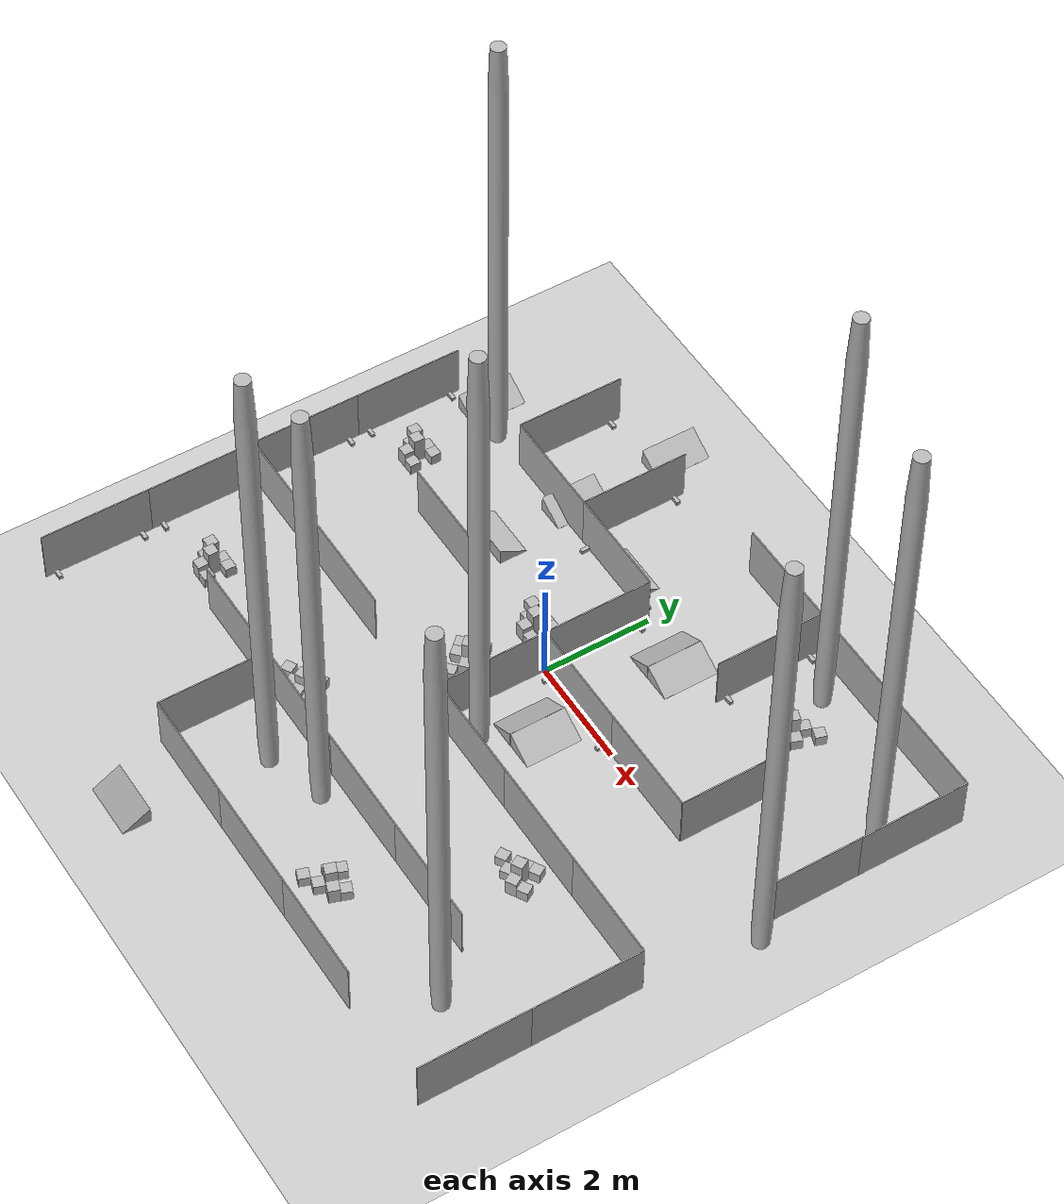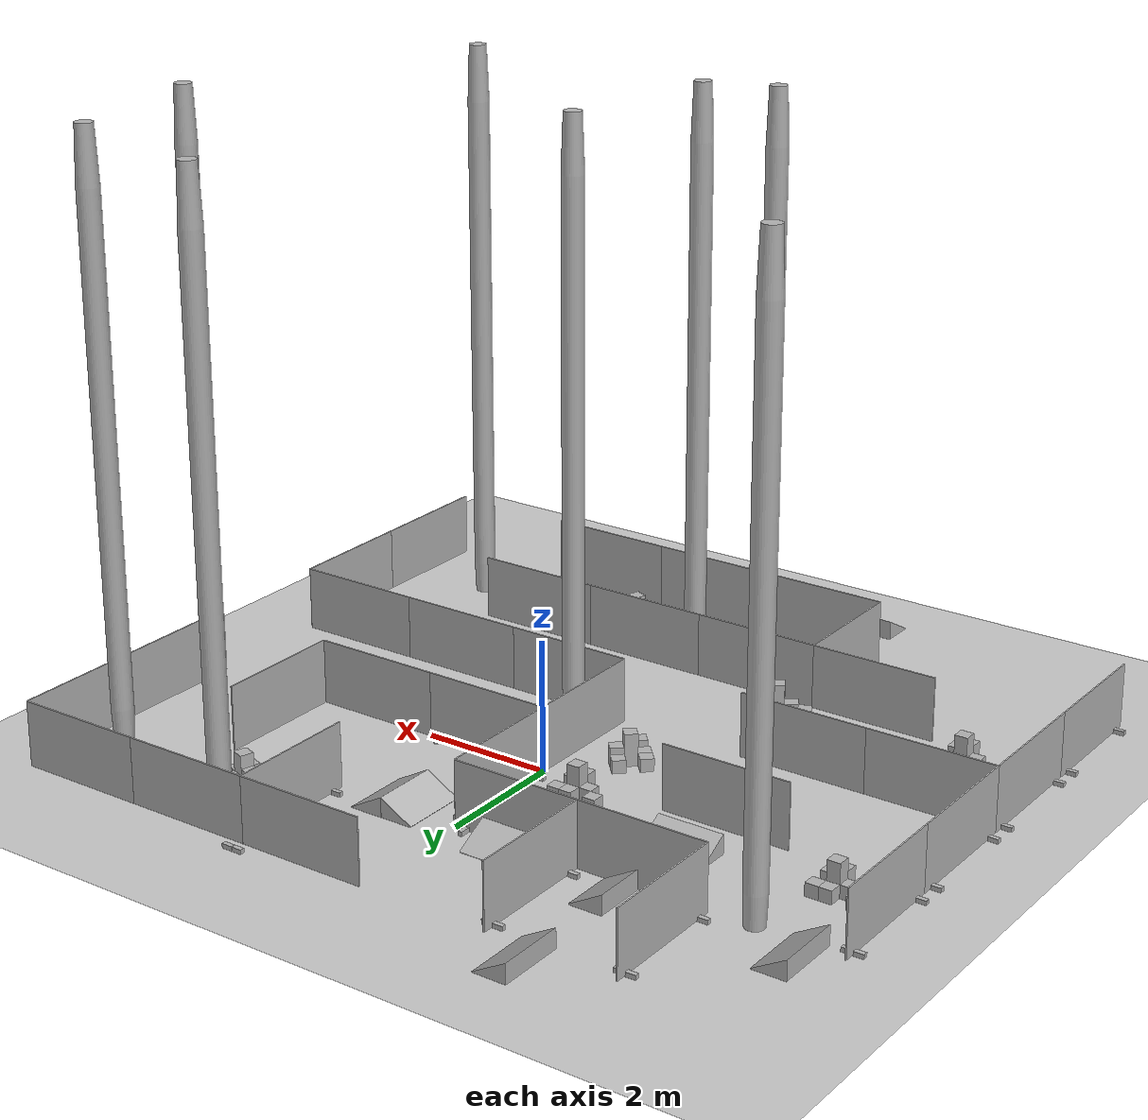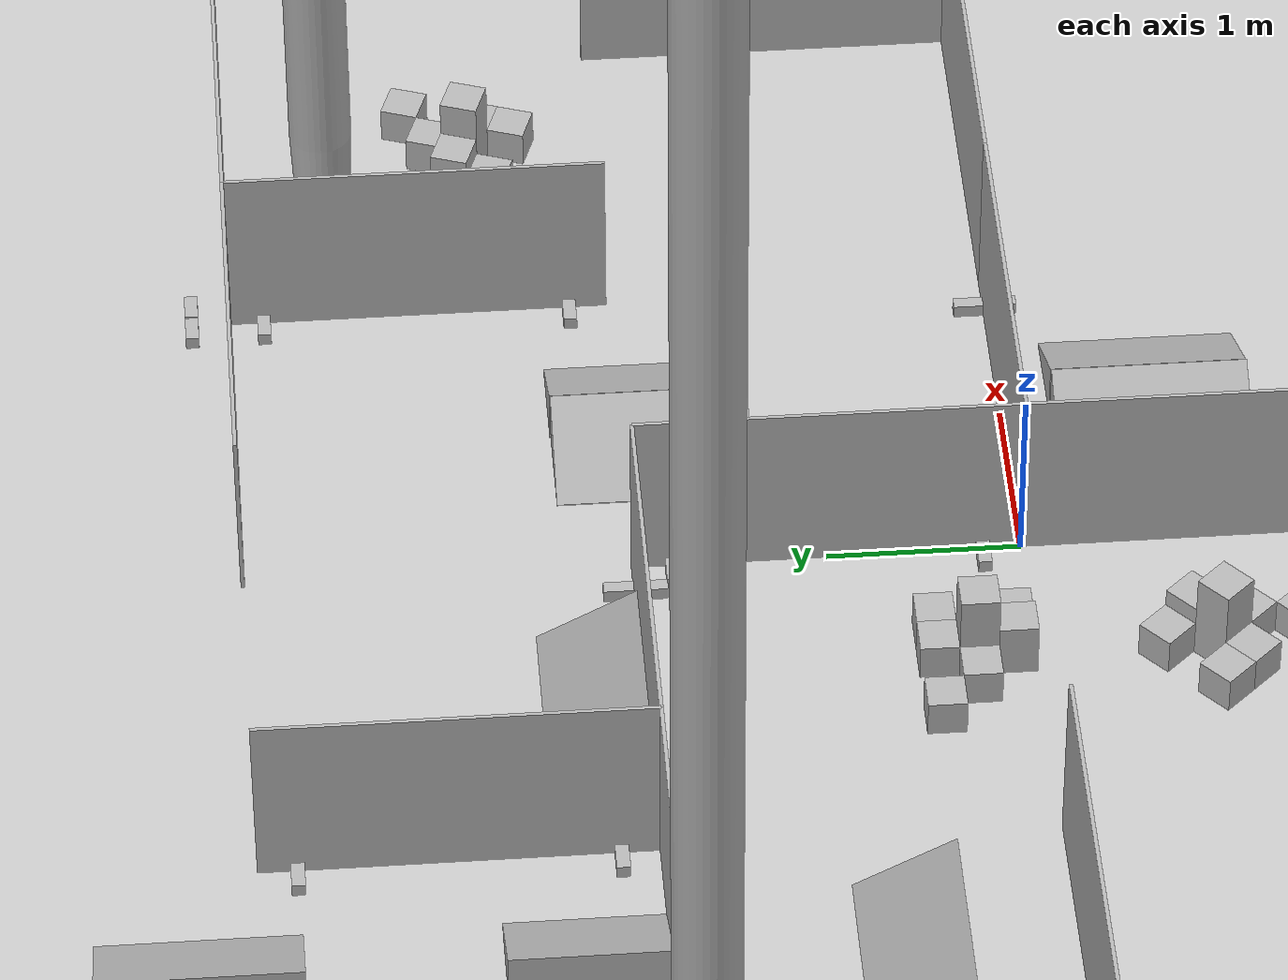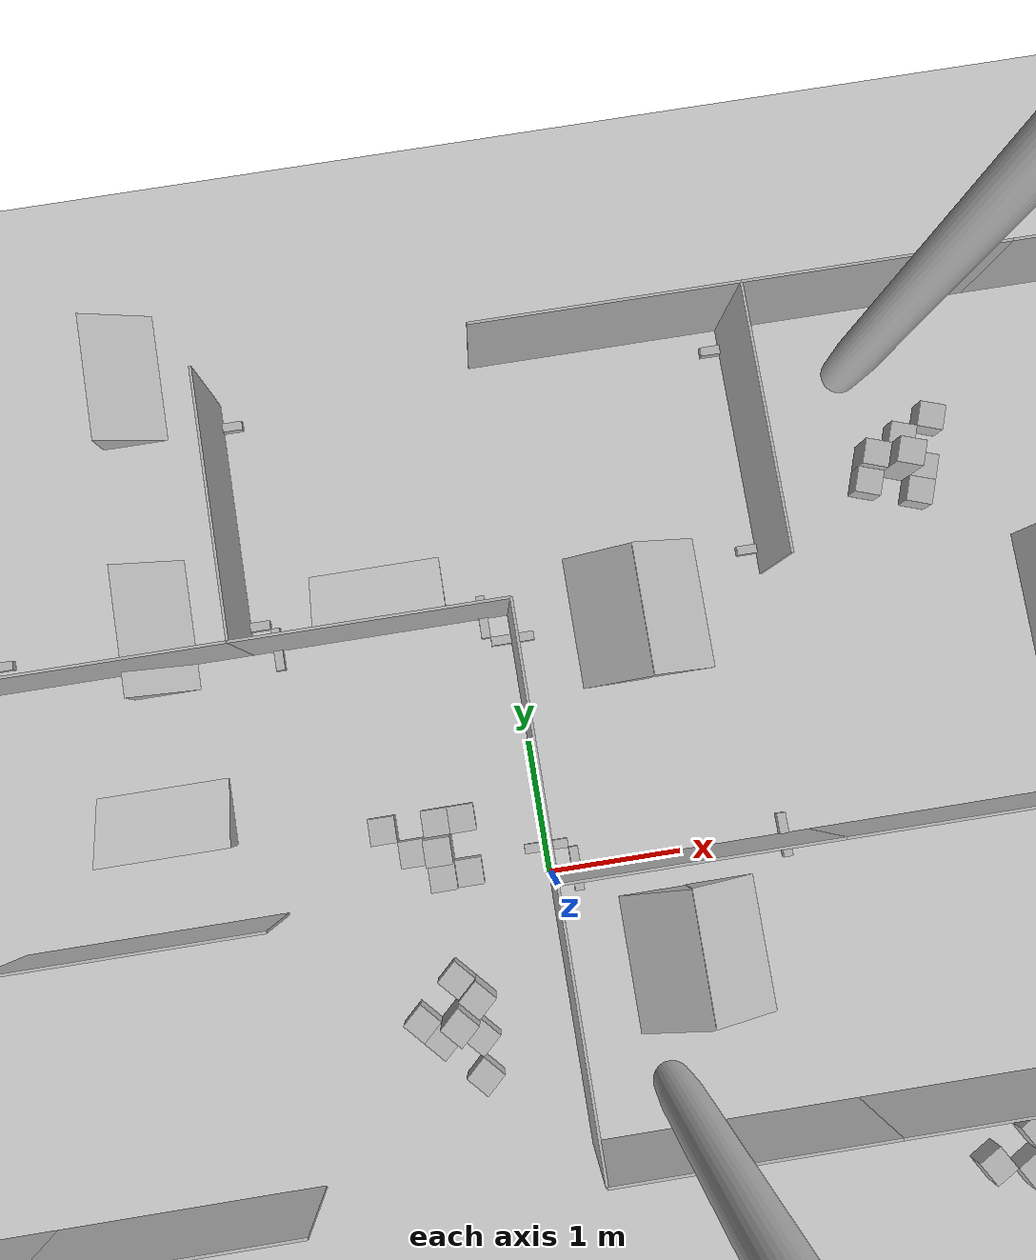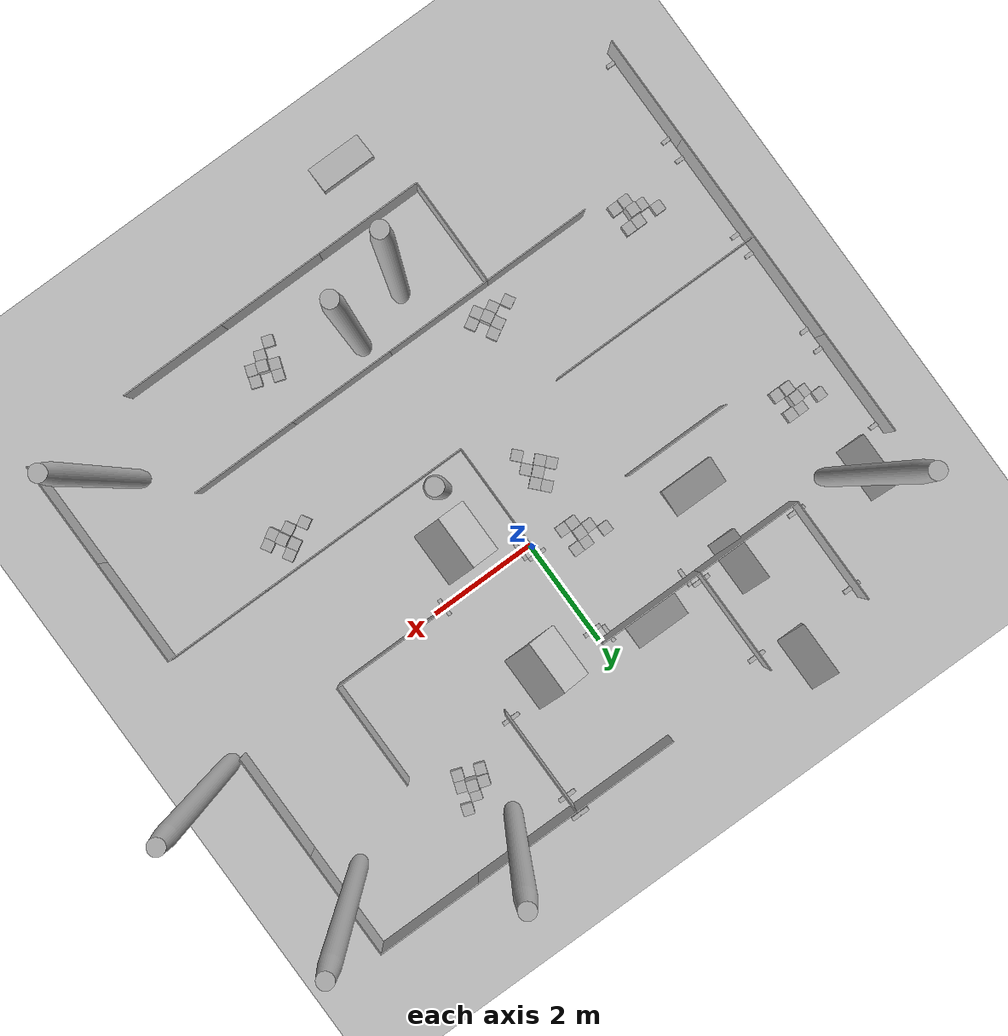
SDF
<sdf version="1.4">
  <!--Generated by blend2world.py-->
  <world name="arena_HKT_1">
    <scene>
      <ambient>0.5 0.5 0.5 1</ambient>
      <background>0.5 0.5 0.5 1</background>
      <shadows>false</shadows>
    </scene>
    <physics type="ode">
      <gravity>0 0 -9.81</gravity>
      <ode>
        <solver>
          <type>quick</type>
          <iters>1000</iters>
          <sor>1.3</sor>
        </solver>
        <constraints>
          <cfm>0.0</cfm>
          <erp>0.2</erp>
          <contact_max_correcting_vel>100.0</contact_max_correcting_vel>
          <contact_surface_layer>0.001</contact_surface_layer>
        </constraints>
      </ode>
      <real_time_update_rate>120</real_time_update_rate>
      <real_time_factor>1</real_time_factor>
      <max_step_size>0.008333</max_step_size>
    </physics>
    <light name="directional_light_1" type="directional">
      <cast_shadows>false</cast_shadows>
      <pose>0 0 30 0.1 0.1 0</pose>
      <diffuse>1.0 1.0 1.0 1</diffuse>
      <specular>.1 .1 .1 1</specular>
      <attenuation>
        <range>300</range>
      </attenuation>
      <direction>0.1 0.1 -1</direction>
    </light>
    <include>
      <uri>model://ground_plane</uri>
    </include>
    <light name="directional_light.-10.0_-12.0" type="sun">
      <pose>-10.0 -12.0 8  0 0 0</pose>
      <cast_shadows>1</cast_shadows>
      <diffuse>0.5 0.5 0.5 1</diffuse>
      <specular>0.1 0.1 0.1 1</specular>
      <attenuation>
        <range>20</range>
        <constant>0.5</constant>
        <linear>0.01</linear>
        <quadratic>0.00</quadratic>
      </attenuation>
      <direction>0.1 0.1 -1.0</direction>
    </light>
    <light name="directional_light.-10.0_0.0" type="sun">
      <pose>-10.0 0.0 8  0 0 0</pose>
      <cast_shadows>1</cast_shadows>
      <diffuse>0.5 0.5 0.5 1</diffuse>
      <specular>0.1 0.1 0.1 1</specular>
      <attenuation>
        <range>20</range>
        <constant>0.5</constant>
        <linear>0.01</linear>
        <quadratic>0.00</quadratic>
      </attenuation>
      <direction>0.1 0.1 -1.0</direction>
    </light>
    <light name="directional_light.-10.0_12.0" type="sun">
      <pose>-10.0 12.0 8  0 0 0</pose>
      <cast_shadows>1</cast_shadows>
      <diffuse>0.5 0.5 0.5 1</diffuse>
      <specular>0.1 0.1 0.1 1</specular>
      <attenuation>
        <range>20</range>
        <constant>0.5</constant>
        <linear>0.01</linear>
        <quadratic>0.00</quadratic>
      </attenuation>
      <direction>0.1 0.1 -1.0</direction>
    </light>
    <light name="directional_light.0.0_-12.0" type="sun">
      <pose>0.0 -12.0 8  0 0 0</pose>
      <cast_shadows>1</cast_shadows>
      <diffuse>0.5 0.5 0.5 1</diffuse>
      <specular>0.1 0.1 0.1 1</specular>
      <attenuation>
        <range>20</range>
        <constant>0.5</constant>
        <linear>0.01</linear>
        <quadratic>0.00</quadratic>
      </attenuation>
      <direction>0.1 0.1 -1.0</direction>
    </light>
    <light name="directional_light.0.0_0.0" type="sun">
      <pose>0.0 0.0 8  0 0 0</pose>
      <cast_shadows>1</cast_shadows>
      <diffuse>0.5 0.5 0.5 1</diffuse>
      <specular>0.1 0.1 0.1 1</specular>
      <attenuation>
        <range>20</range>
        <constant>0.5</constant>
        <linear>0.01</linear>
        <quadratic>0.00</quadratic>
      </attenuation>
      <direction>0.1 0.1 -1.0</direction>
    </light>
    <light name="directional_light.0.0_12.0" type="sun">
      <pose>0.0 12.0 8  0 0 0</pose>
      <cast_shadows>1</cast_shadows>
      <diffuse>0.5 0.5 0.5 1</diffuse>
      <specular>0.1 0.1 0.1 1</specular>
      <attenuation>
        <range>20</range>
        <constant>0.5</constant>
        <linear>0.01</linear>
        <quadratic>0.00</quadratic>
      </attenuation>
      <direction>0.1 0.1 -1.0</direction>
    </light>
    <light name="directional_light.10.0_-12.0" type="sun">
      <pose>10.0 -12.0 8  0 0 0</pose>
      <cast_shadows>1</cast_shadows>
      <diffuse>0.5 0.5 0.5 1</diffuse>
      <specular>0.1 0.1 0.1 1</specular>
      <attenuation>
        <range>20</range>
        <constant>0.5</constant>
        <linear>0.01</linear>
        <quadratic>0.00</quadratic>
      </attenuation>
      <direction>0.1 0.1 -1.0</direction>
    </light>
    <light name="directional_light.10.0_0.0" type="sun">
      <pose>10.0 0.0 8  0 0 0</pose>
      <cast_shadows>1</cast_shadows>
      <diffuse>0.5 0.5 0.5 1</diffuse>
      <specular>0.1 0.1 0.1 1</specular>
      <attenuation>
        <range>20</range>
        <constant>0.5</constant>
        <linear>0.01</linear>
        <quadratic>0.00</quadratic>
      </attenuation>
      <direction>0.1 0.1 -1.0</direction>
    </light>
    <light name="directional_light.10.0_12.0" type="sun">
      <pose>10.0 12.0 8  0 0 0</pose>
      <cast_shadows>1</cast_shadows>
      <diffuse>0.5 0.5 0.5 1</diffuse>
      <specular>0.1 0.1 0.1 1</specular>
      <attenuation>
        <range>20</range>
        <constant>0.5</constant>
        <linear>0.01</linear>
        <quadratic>0.00</quadratic>
      </attenuation>
      <direction>0.1 0.1 -1.0</direction>
    </light>
    <include>
      <name>wall_stand.164</name>
      <pose>2.0 4.19950008392334 0.03449999913573265  0.0 0.0 0.0</pose>
      <uri>model://wall_stand</uri>
    </include>
    <include>
      <name>wall_2x1.078</name>
      <pose>-5.0 -2.0 0.5130000114440918  0.0 0.0 0.0</pose>
      <uri>model://wall_2x1</uri>
    </include>
    <include>
      <name>wall_stand.157</name>
      <pose>-1.8005000352859497 2.0 0.03449999913573265  0.0 -0.0 1.570796251296997</pose>
      <uri>model://wall_stand</uri>
    </include>
    <include>
      <name>wall_stand.156</name>
      <pose>-0.19949999451637268 2.0 0.03449999913573265  0.0 -0.0 1.570796251296997</pose>
      <uri>model://wall_stand</uri>
    </include>
    <include>
      <name>wall_stand.155</name>
      <pose>-6.0 -3.80049991607666 0.03449999913573265  0.0 0.0 0.0</pose>
      <uri>model://wall_stand</uri>
    </include>
    <include>
      <name>wall_stand.154</name>
      <pose>-6.0 -2.1994998455047607 0.03449999913573265  0.0 0.0 0.0</pose>
      <uri>model://wall_stand</uri>
    </include>
    <include>
      <name>wall_2x1.077</name>
      <pose>-6.0 -3.0 0.5130000114440918  0.0 -0.0 1.570796251296997</pose>
      <uri>model://wall_2x1</uri>
    </include>
    <include>
      <name>wall_2x1.076</name>
      <pose>-6.0 -5.0 0.5130000114440918  0.0 -0.0 1.570796251296997</pose>
      <uri>model://wall_2x1</uri>
    </include>
    <include>
      <name>wall_stand.153</name>
      <pose>-6.0 -4.19950008392334 0.03449999913573265  0.0 0.0 0.0</pose>
      <uri>model://wall_stand</uri>
    </include>
    <include>
      <name>wall_stand.152</name>
      <pose>-6.0 -5.80049991607666 0.03449999913573265  0.0 0.0 0.0</pose>
      <uri>model://wall_stand</uri>
    </include>
    <include>
      <name>wall_stand.151</name>
      <pose>-6.0 -1.8004999160766602 0.03449999913573265  0.0 0.0 0.0</pose>
      <uri>model://wall_stand</uri>
    </include>
    <include>
      <name>wall_stand.150</name>
      <pose>-6.0 -0.19949984550476074 0.03449999913573265  0.0 0.0 0.0</pose>
      <uri>model://wall_stand</uri>
    </include>
    <include>
      <name>wall_2x1.075</name>
      <pose>-6.0 -1.0 0.5130000114440918  0.0 -0.0 1.570796251296997</pose>
      <uri>model://wall_2x1</uri>
    </include>
    <include>
      <name>wall_2x1.074</name>
      <pose>5.0 4.0 0.5130000114440918  0.0 0.0 0.0</pose>
      <uri>model://wall_2x1</uri>
    </include>
    <include>
      <name>wall_stand.149</name>
      <pose>-0.19949999451637268 2.0 0.03449999913573265  0.0 -0.0 1.570796251296997</pose>
      <uri>model://wall_stand</uri>
    </include>
    <include>
      <name>wall_stand.148</name>
      <pose>-1.8005000352859497 2.0 0.03449999913573265  0.0 -0.0 1.570796251296997</pose>
      <uri>model://wall_stand</uri>
    </include>
    <include>
      <name>wall_2x1.073</name>
      <pose>3.0 4.0 0.5130000114440918  0.0 0.0 0.0</pose>
      <uri>model://wall_2x1</uri>
    </include>
    <include>
      <name>wall_stand.147</name>
      <pose>-1.8005000352859497 2.0 0.03449999913573265  0.0 -0.0 1.570796251296997</pose>
      <uri>model://wall_stand</uri>
    </include>
    <include>
      <name>wall_stand.146</name>
      <pose>-0.19949999451637268 2.0 0.03449999913573265  0.0 -0.0 1.570796251296997</pose>
      <uri>model://wall_stand</uri>
    </include>
    <include>
      <name>wall_2x1.072</name>
      <pose>1.0 4.0 0.5130000114440918  0.0 0.0 0.0</pose>
      <uri>model://wall_2x1</uri>
    </include>
    <include>
      <name>wall_stand.144</name>
      <pose>-1.8005000352859497 2.0 0.03449999913573265  0.0 -0.0 1.570796251296997</pose>
      <uri>model://wall_stand</uri>
    </include>
    <include>
      <name>wall_2x1.071</name>
      <pose>1.0 -2.0 0.5130000114440918  0.0 0.0 0.0</pose>
      <uri>model://wall_2x1</uri>
    </include>
    <include>
      <name>wall_stand.143</name>
      <pose>-1.8005000352859497 2.0 0.03449999913573265  0.0 -0.0 1.570796251296997</pose>
      <uri>model://wall_stand</uri>
    </include>
    <include>
      <name>wall_stand.142</name>
      <pose>-0.19949999451637268 2.0 0.03449999913573265  0.0 -0.0 1.570796251296997</pose>
      <uri>model://wall_stand</uri>
    </include>
    <include>
      <name>wall_2x1.070</name>
      <pose>3.0 -2.0 0.5130000114440918  0.0 0.0 0.0</pose>
      <uri>model://wall_2x1</uri>
    </include>
    <include>
      <name>wall_stand.141</name>
      <pose>-0.19949999451637268 2.0 0.03449999913573265  0.0 -0.0 1.570796251296997</pose>
      <uri>model://wall_stand</uri>
    </include>
    <include>
      <name>wall_stand.140</name>
      <pose>-1.8005000352859497 2.0 0.03449999913573265  0.0 -0.0 1.570796251296997</pose>
      <uri>model://wall_stand</uri>
    </include>
    <include>
      <name>wall_2x1.069</name>
      <pose>5.0 -2.0 0.5130000114440918  0.0 0.0 0.0</pose>
      <uri>model://wall_2x1</uri>
    </include>
    <include>
      <name>wall_stand.139</name>
      <pose>-1.8005000352859497 2.0 0.03449999913573265  0.0 -0.0 1.570796251296997</pose>
      <uri>model://wall_stand</uri>
    </include>
    <include>
      <name>wall_stand.138</name>
      <pose>-0.19949999451637268 2.0 0.03449999913573265  0.0 -0.0 1.570796251296997</pose>
      <uri>model://wall_stand</uri>
    </include>
    <include>
      <name>wall_2x1.068</name>
      <pose>6.0 -3.0 0.5130000114440918  0.0 -0.0 1.570796251296997</pose>
      <uri>model://wall_2x1</uri>
    </include>
    <include>
      <name>wall_stand.137</name>
      <pose>0.0 1.8005001544952393 0.03449999913573265  0.0 0.0 0.0</pose>
      <uri>model://wall_stand</uri>
    </include>
    <include>
      <name>wall_stand.136</name>
      <pose>0.0 0.19949999451637268 0.03449999913573265  0.0 0.0 0.0</pose>
      <uri>model://wall_stand</uri>
    </include>
    <include>
      <name>wall_2x1.067</name>
      <pose>6.0 -5.0 0.5130000114440918  0.0 -0.0 1.570796251296997</pose>
      <uri>model://wall_2x1</uri>
    </include>
    <include>
      <name>wall_stand.135</name>
      <pose>0.0 0.19949999451637268 0.03449999913573265  0.0 0.0 0.0</pose>
      <uri>model://wall_stand</uri>
    </include>
    <include>
      <name>wall_stand.134</name>
      <pose>0.0 1.8005001544952393 0.03449999913573265  0.0 0.0 0.0</pose>
      <uri>model://wall_stand</uri>
    </include>
    <include>
      <name>wall_2x1.066</name>
      <pose>-2.0 -5.0 0.5130000114440918  0.0 -0.0 1.570796251296997</pose>
      <uri>model://wall_2x1</uri>
    </include>
    <include>
      <name>wall_stand.133</name>
      <pose>0.0 0.19949999451637268 0.03449999913573265  0.0 0.0 0.0</pose>
      <uri>model://wall_stand</uri>
    </include>
    <include>
      <name>wall_stand.132</name>
      <pose>0.0 1.8005001544952393 0.03449999913573265  0.0 0.0 0.0</pose>
      <uri>model://wall_stand</uri>
    </include>
    <include>
      <name>wall_2x1.065</name>
      <pose>-1.0 -6.0 0.5130000114440918  0.0 0.0 0.0</pose>
      <uri>model://wall_2x1</uri>
    </include>
    <include>
      <name>wall_stand.131</name>
      <pose>-1.8005000352859497 2.0 0.03449999913573265  0.0 -0.0 1.570796251296997</pose>
      <uri>model://wall_stand</uri>
    </include>
    <include>
      <name>wall_stand.130</name>
      <pose>-0.19949999451637268 2.0 0.03449999913573265  0.0 -0.0 1.570796251296997</pose>
      <uri>model://wall_stand</uri>
    </include>
    <include>
      <name>wall_2x1.064</name>
      <pose>1.0 -6.0 0.5130000114440918  0.0 0.0 0.0</pose>
      <uri>model://wall_2x1</uri>
    </include>
    <include>
      <name>wall_stand.129</name>
      <pose>-0.19949999451637268 2.0 0.03449999913573265  0.0 -0.0 1.570796251296997</pose>
      <uri>model://wall_stand</uri>
    </include>
    <include>
      <name>wall_stand.128</name>
      <pose>-1.8005000352859497 2.0 0.03449999913573265  0.0 -0.0 1.570796251296997</pose>
      <uri>model://wall_stand</uri>
    </include>
    <include>
      <name>wall_2x1.063</name>
      <pose>3.0 -6.0 0.5130000114440918  0.0 0.0 0.0</pose>
      <uri>model://wall_2x1</uri>
    </include>
    <include>
      <name>wall_stand.127</name>
      <pose>-1.8005000352859497 2.0 0.03449999913573265  0.0 -0.0 1.570796251296997</pose>
      <uri>model://wall_stand</uri>
    </include>
    <include>
      <name>wall_stand.126</name>
      <pose>-0.19949999451637268 2.0 0.03449999913573265  0.0 -0.0 1.570796251296997</pose>
      <uri>model://wall_stand</uri>
    </include>
    <include>
      <name>wall_2x1.062</name>
      <pose>6.0 1.0 0.5130000114440918  0.0 -0.0 1.570796251296997</pose>
      <uri>model://wall_2x1</uri>
    </include>
    <include>
      <name>wall_stand.125</name>
      <pose>0.0 1.8005001544952393 0.03449999913573265  0.0 0.0 0.0</pose>
      <uri>model://wall_stand</uri>
    </include>
    <include>
      <name>wall_stand.124</name>
      <pose>0.0 0.19949999451637268 0.03449999913573265  0.0 0.0 0.0</pose>
      <uri>model://wall_stand</uri>
    </include>
    <include>
      <name>wall_2x1.061</name>
      <pose>6.0 3.0 0.5130000114440918  0.0 -0.0 1.570796251296997</pose>
      <uri>model://wall_2x1</uri>
    </include>
    <include>
      <name>wall_stand.123</name>
      <pose>0.0 0.19949999451637268 0.03449999913573265  0.0 0.0 0.0</pose>
      <uri>model://wall_stand</uri>
    </include>
    <include>
      <name>wall_stand.122</name>
      <pose>0.0 1.8005001544952393 0.03449999913573265  0.0 0.0 0.0</pose>
      <uri>model://wall_stand</uri>
    </include>
    <include>
      <name>wall_stand.120</name>
      <pose>0.0 0.19949999451637268 0.03449999913573265  0.0 0.0 0.0</pose>
      <uri>model://wall_stand</uri>
    </include>
    <include>
      <name>wall_stand.095</name>
      <pose>-1.8005000352859497 2.0 0.03449999913573265  0.0 -0.0 1.570796251296997</pose>
      <uri>model://wall_stand</uri>
    </include>
    <include>
      <name>wall_stand.089</name>
      <pose>-0.19949999451637268 2.0 0.03449999913573265  0.0 -0.0 1.570796251296997</pose>
      <uri>model://wall_stand</uri>
    </include>
    <include>
      <name>wall_stand.086</name>
      <pose>-0.19949999451637268 2.0 0.03449999913573265  0.0 -0.0 1.570796251296997</pose>
      <uri>model://wall_stand</uri>
    </include>
    <include>
      <name>wall_stand.072</name>
      <pose>0.0 1.8005001544952393 0.03449999913573265  0.0 0.0 0.0</pose>
      <uri>model://wall_stand</uri>
    </include>
    <include>
      <name>wall_stand.067</name>
      <pose>0.0 0.19949999451637268 0.03449999913573265  0.0 0.0 0.0</pose>
      <uri>model://wall_stand</uri>
    </include>
    <include>
      <name>wall_stand.057</name>
      <pose>-1.8005000352859497 2.0 0.03449999913573265  0.0 -0.0 1.570796251296997</pose>
      <uri>model://wall_stand</uri>
    </include>
    <include>
      <name>wall_2x1.025</name>
      <pose>0.0 -1.0 0.5130000114440918  0.0 -0.0 1.570796251296997</pose>
      <uri>model://wall_2x1</uri>
    </include>
    <include>
      <name>wall_stand.051</name>
      <pose>0.0 0.19949999451637268 0.03449999913573265  0.0 0.0 0.0</pose>
      <uri>model://wall_stand</uri>
    </include>
    <include>
      <name>wall_stand.050</name>
      <pose>0.0 1.8005001544952393 0.03449999913573265  0.0 0.0 0.0</pose>
      <uri>model://wall_stand</uri>
    </include>
    <include>
      <name>wall_2x1.024</name>
      <pose>3.0 -4.0 0.5130000114440918  0.0 0.0 0.0</pose>
      <uri>model://wall_2x1</uri>
    </include>
    <include>
      <name>wall_stand.049</name>
      <pose>-0.19949999451637268 2.0 0.03449999913573265  0.0 -0.0 1.570796251296997</pose>
      <uri>model://wall_stand</uri>
    </include>
    <include>
      <name>wall_stand.048</name>
      <pose>-1.8005000352859497 2.0 0.03449999913573265  0.0 -0.0 1.570796251296997</pose>
      <uri>model://wall_stand</uri>
    </include>
    <include>
      <name>wall_2x1.023</name>
      <pose>1.0 -4.0 0.5130000114440918  0.0 0.0 0.0</pose>
      <uri>model://wall_2x1</uri>
    </include>
    <include>
      <name>wall_stand.047</name>
      <pose>-1.8005000352859497 2.0 0.03449999913573265  0.0 -0.0 1.570796251296997</pose>
      <uri>model://wall_stand</uri>
    </include>
    <include>
      <name>wall_stand.046</name>
      <pose>-0.19949999451637268 2.0 0.03449999913573265  0.0 -0.0 1.570796251296997</pose>
      <uri>model://wall_stand</uri>
    </include>
    <include>
      <name>wall_2x1.022</name>
      <pose>-1.0 -4.0 0.5130000114440918  0.0 0.0 0.0</pose>
      <uri>model://wall_2x1</uri>
    </include>
    <include>
      <name>wall_stand.045</name>
      <pose>-0.19949999451637268 2.0 0.03449999913573265  0.0 -0.0 1.570796251296997</pose>
      <uri>model://wall_stand</uri>
    </include>
    <include>
      <name>wall_stand.044</name>
      <pose>-1.8005000352859497 2.0 0.03449999913573265  0.0 -0.0 1.570796251296997</pose>
      <uri>model://wall_stand</uri>
    </include>
    <include>
      <name>wall_2x1.021</name>
      <pose>-3.0 -4.0 0.5130000114440918  0.0 0.0 0.0</pose>
      <uri>model://wall_2x1</uri>
    </include>
    <include>
      <name>wall_stand.043</name>
      <pose>-1.8005000352859497 2.0 0.03449999913573265  0.0 -0.0 1.570796251296997</pose>
      <uri>model://wall_stand</uri>
    </include>
    <include>
      <name>wall_stand.042</name>
      <pose>-0.19949999451637268 2.0 0.03449999913573265  0.0 -0.0 1.570796251296997</pose>
      <uri>model://wall_stand</uri>
    </include>
    <include>
      <name>wall_2x1.020</name>
      <pose>-3.0 -2.0 0.5130000114440918  0.0 0.0 0.0</pose>
      <uri>model://wall_2x1</uri>
    </include>
    <include>
      <name>wall_stand.041</name>
      <pose>-0.19949999451637268 2.0 0.03449999913573265  0.0 -0.0 1.570796251296997</pose>
      <uri>model://wall_stand</uri>
    </include>
    <include>
      <name>wall_stand.040</name>
      <pose>-1.8005000352859497 2.0 0.03449999913573265  0.0 -0.0 1.570796251296997</pose>
      <uri>model://wall_stand</uri>
    </include>
    <include>
      <name>wall_2x1.019</name>
      <pose>3.0 0.0 0.5130000114440918  0.0 0.0 0.0</pose>
      <uri>model://wall_2x1</uri>
    </include>
    <include>
      <name>wall_stand.039</name>
      <pose>0.19949999451637268 0.0 0.03449999913573265  0.0 -0.0 1.570796251296997</pose>
      <uri>model://wall_stand</uri>
    </include>
    <include>
      <name>wall_stand.038</name>
      <pose>1.8005000352859497 0.0 0.03449999913573265  0.0 -0.0 1.570796251296997</pose>
      <uri>model://wall_stand</uri>
    </include>
    <include>
      <name>wall_2x1.018</name>
      <pose>4.0 1.0 0.5130000114440918  0.0 -0.0 1.570796251296997</pose>
      <uri>model://wall_2x1</uri>
    </include>
    <include>
      <name>wall_stand.037</name>
      <pose>0.0 0.19949999451637268 0.03449999913573265  0.0 0.0 0.0</pose>
      <uri>model://wall_stand</uri>
    </include>
    <include>
      <name>wall_stand.036</name>
      <pose>0.0 1.8005001544952393 0.03449999913573265  0.0 0.0 0.0</pose>
      <uri>model://wall_stand</uri>
    </include>
    <include>
      <name>wall_2x1.017</name>
      <pose>-3.0 0.0 0.5130000114440918  0.0 0.0 0.0</pose>
      <uri>model://wall_2x1</uri>
    </include>
    <include>
      <name>wall_stand.035</name>
      <pose>-1.8005000352859497 2.0 0.03449999913573265  0.0 -0.0 1.570796251296997</pose>
      <uri>model://wall_stand</uri>
    </include>
    <include>
      <name>wall_stand.034</name>
      <pose>-0.19949999451637268 2.0 0.03449999913573265  0.0 -0.0 1.570796251296997</pose>
      <uri>model://wall_stand</uri>
    </include>
    <include>
      <name>wall_2x1.016</name>
      <pose>-3.0 2.0 0.5130000114440918  0.0 0.0 0.0</pose>
      <uri>model://wall_2x1</uri>
    </include>
    <include>
      <name>wall_stand.033</name>
      <pose>-0.19949999451637268 2.0 0.03449999913573265  0.0 -0.0 1.570796251296997</pose>
      <uri>model://wall_stand</uri>
    </include>
    <include>
      <name>wall_stand.032</name>
      <pose>-1.8005000352859497 2.0 0.03449999913573265  0.0 -0.0 1.570796251296997</pose>
      <uri>model://wall_stand</uri>
    </include>
    <include>
      <name>cube_20x20.005</name>
      <pose>-0.800000011920929 0.5099999904632568 0.10000000149011612  0.0 -0.0 3.141592502593994</pose>
      <uri>model://cube_20x20</uri>
    </include>
    <include>
      <name>cube_20x20.006</name>
      <pose>-1.0 0.3100000023841858 0.10000000149011612  0.0 -0.0 3.141592502593994</pose>
      <uri>model://cube_20x20</uri>
    </include>
    <include>
      <name>cube_20x20.007</name>
      <pose>-1.2000000476837158 0.5099999904632568 0.10000000149011612  0.0 -0.0 3.141592502593994</pose>
      <uri>model://cube_20x20</uri>
    </include>
    <include>
      <name>cube_20x20.008</name>
      <pose>-0.6000000238418579 0.5099999904632568 0.10000000149011612  0.0 -0.0 3.141592502593994</pose>
      <uri>model://cube_20x20</uri>
    </include>
    <include>
      <name>cube_20x20.009</name>
      <pose>-0.6000000238418579 0.10999999940395355 0.10000000149011612  0.0 -0.0 3.141592502593994</pose>
      <uri>model://cube_20x20</uri>
    </include>
    <include>
      <name>cube_20x30.001</name>
      <pose>-0.800000011920929 0.10999999940395355 0.15000000596046448  0.0 -0.0 3.141592502593994</pose>
      <uri>model://cube_20x30</uri>
    </include>
    <include>
      <name>cube_20x50.001</name>
      <pose>-0.800000011920929 0.3100000023841858 0.25  0.0 -0.0 3.141592502593994</pose>
      <uri>model://cube_20x50</uri>
    </include>
    <include>
      <name>ramp.006</name>
      <pose>-1.2133511304855347 -7.135537147521973 0.15000000596046448  0.0 -0.0 4.71238899230957</pose>
      <uri>model://ramp</uri>
    </include>
    <include>
      <name>ramp.007</name>
      <pose>-0.9832800030708313 2.2666399478912354 0.15000000596046448  0.0 -0.0 7.853981971740723</pose>
      <uri>model://ramp</uri>
    </include>
    <include>
      <name>wall_2x1.009</name>
      <pose>1.0 0.0 0.5130000114440918  0.0 0.0 0.0</pose>
      <uri>model://wall_2x1</uri>
    </include>
    <include>
      <name>wall_stand.019</name>
      <pose>1.8005000352859497 0.0 0.03449999913573265  0.0 -0.0 1.570796251296997</pose>
      <uri>model://wall_stand</uri>
    </include>
    <include>
      <name>wall_stand.017</name>
      <pose>0.19949999451637268 0.0 0.03449999913573265  0.0 -0.0 1.570796251296997</pose>
      <uri>model://wall_stand</uri>
    </include>
    <include>
      <name>wall_2x1.010</name>
      <pose>0.0 1.0 0.5130000114440918  0.0 -0.0 1.570796251296997</pose>
      <uri>model://wall_2x1</uri>
    </include>
    <include>
      <name>wall_stand.025</name>
      <pose>0.0 1.8005001544952393 0.03449999913573265  0.0 0.0 0.0</pose>
      <uri>model://wall_stand</uri>
    </include>
    <include>
      <name>wall_stand.013</name>
      <pose>0.0 0.19949999451637268 0.03449999913573265  0.0 0.0 0.0</pose>
      <uri>model://wall_stand</uri>
    </include>
    <include>
      <name>wall_2x1.011</name>
      <pose>-4.0 3.0 0.5130000114440918  0.0 -0.0 1.570796251296997</pose>
      <uri>model://wall_2x1</uri>
    </include>
    <include>
      <name>wall_2x1.012</name>
      <pose>-2.0 3.0 0.5130000114440918  0.0 -0.0 1.570796251296997</pose>
      <uri>model://wall_2x1</uri>
    </include>
    <include>
      <name>wall_2x1.013</name>
      <pose>-6.0 1.0 0.5130000114440918  0.0 -0.0 1.570796251296997</pose>
      <uri>model://wall_2x1</uri>
    </include>
    <include>
      <name>wall_2x1.014</name>
      <pose>2.0 3.0 0.5130000114440918  0.0 -0.0 1.570796251296997</pose>
      <uri>model://wall_2x1</uri>
    </include>
    <include>
      <name>wall_2x1.015</name>
      <pose>-1.0 2.0 0.5130000114440918  0.0 0.0 0.0</pose>
      <uri>model://wall_2x1</uri>
    </include>
    <include>
      <name>wall_stand.030</name>
      <pose>-1.8005000352859497 2.0 0.03449999913573265  0.0 -0.0 1.570796251296997</pose>
      <uri>model://wall_stand</uri>
    </include>
    <include>
      <name>wall_stand.024</name>
      <pose>-0.19949999451637268 2.0 0.03449999913573265  0.0 -0.0 1.570796251296997</pose>
      <uri>model://wall_stand</uri>
    </include>
    <include>
      <name>wall_stand.021</name>
      <pose>-4.0 2.19950008392334 0.03449999913573265  0.0 0.0 0.0</pose>
      <uri>model://wall_stand</uri>
    </include>
    <include>
      <name>wall_stand.022</name>
      <pose>2.0 2.19950008392334 0.03449999913573265  0.0 0.0 0.0</pose>
      <uri>model://wall_stand</uri>
    </include>
    <include>
      <name>wall_stand.023</name>
      <pose>-2.0 2.19950008392334 0.03449999913573265  0.0 0.0 0.0</pose>
      <uri>model://wall_stand</uri>
    </include>
    <include>
      <name>wall_stand.026</name>
      <pose>2.0 3.817974328994751 0.03449999913573265  0.0 0.0 0.0</pose>
      <uri>model://wall_stand</uri>
    </include>
    <include>
      <name>wall_stand.027</name>
      <pose>-2.0 3.8005001544952393 0.03449999913573265  0.0 0.0 0.0</pose>
      <uri>model://wall_stand</uri>
    </include>
    <include>
      <name>wall_stand.028</name>
      <pose>-6.0 1.8005001544952393 0.03449999913573265  0.0 0.0 0.0</pose>
      <uri>model://wall_stand</uri>
    </include>
    <include>
      <name>wall_stand.029</name>
      <pose>-6.0 0.19950008392333984 0.03449999913573265  0.0 0.0 0.0</pose>
      <uri>model://wall_stand</uri>
    </include>
    <include>
      <name>wall_stand.031</name>
      <pose>-4.0 3.8005001544952393 0.03449999913573265  0.0 0.0 0.0</pose>
      <uri>model://wall_stand</uri>
    </include>
    <include>
      <name>cube_20x20.110</name>
      <pose>-5.073810577392578 0.8086726665496826 0.10000000149011612  0.0 -0.0 3.141592502593994</pose>
      <uri>model://cube_20x20</uri>
    </include>
    <include>
      <name>cube_20x20.111</name>
      <pose>-5.273810386657715 0.6086728572845459 0.10000000149011612  0.0 -0.0 3.141592502593994</pose>
      <uri>model://cube_20x20</uri>
    </include>
    <include>
      <name>cube_20x20.112</name>
      <pose>-5.473810195922852 0.8086726665496826 0.10000000149011612  0.0 -0.0 3.141592502593994</pose>
      <uri>model://cube_20x20</uri>
    </include>
    <include>
      <name>cube_20x20.113</name>
      <pose>-4.873810291290283 0.8086726665496826 0.10000000149011612  0.0 -0.0 3.141592502593994</pose>
      <uri>model://cube_20x20</uri>
    </include>
    <include>
      <name>cube_20x20.114</name>
      <pose>-4.873810291290283 0.4086730480194092 0.10000000149011612  0.0 -0.0 3.141592502593994</pose>
      <uri>model://cube_20x20</uri>
    </include>
    <include>
      <name>cube_20x20.115</name>
      <pose>-5.073810577392578 0.8086726665496826 0.10000000149011612  0.0 -0.0 3.141592502593994</pose>
      <uri>model://cube_20x20</uri>
    </include>
    <include>
      <name>cube_20x20.116</name>
      <pose>-5.273810386657715 0.6086728572845459 0.10000000149011612  0.0 -0.0 3.141592502593994</pose>
      <uri>model://cube_20x20</uri>
    </include>
    <include>
      <name>cube_20x20.117</name>
      <pose>-5.473810195922852 0.8086726665496826 0.10000000149011612  0.0 -0.0 3.141592502593994</pose>
      <uri>model://cube_20x20</uri>
    </include>
    <include>
      <name>cube_20x20.118</name>
      <pose>-4.873810291290283 0.8086726665496826 0.10000000149011612  0.0 -0.0 3.141592502593994</pose>
      <uri>model://cube_20x20</uri>
    </include>
    <include>
      <name>cube_20x20.119</name>
      <pose>-4.873810291290283 0.4086730480194092 0.10000000149011612  0.0 -0.0 3.141592502593994</pose>
      <uri>model://cube_20x20</uri>
    </include>
    <include>
      <name>cube_20x20.120</name>
      <pose>-4.71690034866333 -3.3630831241607666 0.10000000149011612  0.0 -0.0 3.141592502593994</pose>
      <uri>model://cube_20x20</uri>
    </include>
    <include>
      <name>cube_20x20.121</name>
      <pose>-4.916900157928467 -3.5630829334259033 0.10000000149011612  0.0 -0.0 3.141592502593994</pose>
      <uri>model://cube_20x20</uri>
    </include>
    <include>
      <name>cube_20x20.122</name>
      <pose>-5.1168999671936035 -3.3630831241607666 0.10000000149011612  0.0 -0.0 3.141592502593994</pose>
      <uri>model://cube_20x20</uri>
    </include>
    <include>
      <name>cube_20x20.123</name>
      <pose>-4.516900062561035 -3.3630831241607666 0.10000000149011612  0.0 -0.0 3.141592502593994</pose>
      <uri>model://cube_20x20</uri>
    </include>
    <include>
      <name>cube_20x20.124</name>
      <pose>-4.516900062561035 -3.76308274269104 0.10000000149011612  0.0 -0.0 3.141592502593994</pose>
      <uri>model://cube_20x20</uri>
    </include>
    <include>
      <name>cube_20x20.125</name>
      <pose>-4.71690034866333 -3.3630831241607666 0.10000000149011612  0.0 -0.0 3.141592502593994</pose>
      <uri>model://cube_20x20</uri>
    </include>
    <include>
      <name>cube_20x20.126</name>
      <pose>-4.916900157928467 -3.5630829334259033 0.10000000149011612  0.0 -0.0 3.141592502593994</pose>
      <uri>model://cube_20x20</uri>
    </include>
    <include>
      <name>cube_20x20.127</name>
      <pose>-5.1168999671936035 -3.3630831241607666 0.10000000149011612  0.0 -0.0 3.141592502593994</pose>
      <uri>model://cube_20x20</uri>
    </include>
    <include>
      <name>cube_20x20.128</name>
      <pose>-4.516900062561035 -3.3630831241607666 0.10000000149011612  0.0 -0.0 3.141592502593994</pose>
      <uri>model://cube_20x20</uri>
    </include>
    <include>
      <name>cube_20x20.129</name>
      <pose>-4.516900062561035 -3.76308274269104 0.10000000149011612  0.0 -0.0 3.141592502593994</pose>
      <uri>model://cube_20x20</uri>
    </include>
    <include>
      <name>cube_20x20.130</name>
      <pose>-1.7805752754211426 -3.3717634677886963 0.10000000149011612  0.0 -0.0 3.6651763916015625</pose>
      <uri>model://cube_20x20</uri>
    </include>
    <include>
      <name>cube_20x20.131</name>
      <pose>-1.8537843227386475 -3.6449673175811768 0.10000000149011612  0.0 -0.0 3.6651763916015625</pose>
      <uri>model://cube_20x20</uri>
    </include>
    <include>
      <name>cube_20x20.132</name>
      <pose>-2.126988172531128 -3.5717580318450928 0.10000000149011612  0.0 -0.0 3.6651763916015625</pose>
      <uri>model://cube_20x20</uri>
    </include>
    <include>
      <name>cube_20x20.133</name>
      <pose>-1.6073683500289917 -3.271765947341919 0.10000000149011612  0.0 -0.0 3.6651763916015625</pose>
      <uri>model://cube_20x20</uri>
    </include>
    <include>
      <name>cube_20x20.134</name>
      <pose>-1.4073739051818848 -3.6181790828704834 0.10000000149011612  0.0 -0.0 3.6651763916015625</pose>
      <uri>model://cube_20x20</uri>
    </include>
    <include>
      <name>cube_20x20.135</name>
      <pose>-1.7805752754211426 -3.3717634677886963 0.10000000149011612  0.0 -0.0 3.6651763916015625</pose>
      <uri>model://cube_20x20</uri>
    </include>
    <include>
      <name>cube_20x20.136</name>
      <pose>-1.8537843227386475 -3.6449673175811768 0.10000000149011612  0.0 -0.0 3.6651763916015625</pose>
      <uri>model://cube_20x20</uri>
    </include>
    <include>
      <name>cube_20x20.137</name>
      <pose>-2.126988172531128 -3.5717580318450928 0.10000000149011612  0.0 -0.0 3.6651763916015625</pose>
      <uri>model://cube_20x20</uri>
    </include>
    <include>
      <name>cube_20x20.138</name>
      <pose>-1.6073683500289917 -3.271765947341919 0.10000000149011612  0.0 -0.0 3.6651763916015625</pose>
      <uri>model://cube_20x20</uri>
    </include>
    <include>
      <name>cube_20x20.139</name>
      <pose>-1.4073739051818848 -3.6181790828704834 0.10000000149011612  0.0 -0.0 3.6651763916015625</pose>
      <uri>model://cube_20x20</uri>
    </include>
    <include>
      <name>cube_20x20.152</name>
      <pose>-0.978894829750061 -1.071094274520874 0.10000000149011612  0.0 0.0 5.4528021812438965</pose>
      <uri>model://cube_20x20</uri>
    </include>
    <include>
      <name>cube_20x20.153</name>
      <pose>-0.6963385343551636 -1.0838134288787842 0.10000000149011612  0.0 0.0 5.4528021812438965</pose>
      <uri>model://cube_20x20</uri>
    </include>
    <include>
      <name>cube_20x20.154</name>
      <pose>-0.709058403968811 -1.3663697242736816 0.10000000149011612  0.0 0.0 5.4528021812438965</pose>
      <uri>model://cube_20x20</uri>
    </include>
    <include>
      <name>cube_20x20.155</name>
      <pose>-1.1138131618499756 -0.9234559535980225 0.10000000149011612  0.0 0.0 5.4528021812438965</pose>
      <uri>model://cube_20x20</uri>
    </include>
    <include>
      <name>cube_20x20.156</name>
      <pose>-0.8185372948646545 -0.6536192893981934 0.10000000149011612  0.0 0.0 5.4528021812438965</pose>
      <uri>model://cube_20x20</uri>
    </include>
    <include>
      <name>cube_20x20.157</name>
      <pose>-0.978894829750061 -1.071094274520874 0.10000000149011612  0.0 0.0 5.4528021812438965</pose>
      <uri>model://cube_20x20</uri>
    </include>
    <include>
      <name>cube_20x20.158</name>
      <pose>-0.6963385343551636 -1.0838134288787842 0.10000000149011612  0.0 0.0 5.4528021812438965</pose>
      <uri>model://cube_20x20</uri>
    </include>
    <include>
      <name>cube_20x20.159</name>
      <pose>-0.709058403968811 -1.3663697242736816 0.10000000149011612  0.0 0.0 5.4528021812438965</pose>
      <uri>model://cube_20x20</uri>
    </include>
    <include>
      <name>cube_20x20.160</name>
      <pose>-1.1138131618499756 -0.9234559535980225 0.10000000149011612  0.0 0.0 5.4528021812438965</pose>
      <uri>model://cube_20x20</uri>
    </include>
    <include>
      <name>cube_20x20.161</name>
      <pose>-0.8185372948646545 -0.6536192893981934 0.10000000149011612  0.0 0.0 5.4528021812438965</pose>
      <uri>model://cube_20x20</uri>
    </include>
    <include>
      <name>cube_20x20.172</name>
      <pose>3.3604865074157715 2.6194584369659424 0.10000000149011612  0.0 0.0 7.517675399780273</pose>
      <uri>model://cube_20x20</uri>
    </include>
    <include>
      <name>cube_20x20.173</name>
      <pose>3.2376906871795654 2.8742544651031494 0.10000000149011612  0.0 0.0 7.517675399780273</pose>
      <uri>model://cube_20x20</uri>
    </include>
    <include>
      <name>cube_20x20.174</name>
      <pose>3.4924871921539307 2.9970500469207764 0.10000000149011612  0.0 0.0 7.517675399780273</pose>
      <uri>model://cube_20x20</uri>
    </include>
    <include>
      <name>cube_20x20.175</name>
      <pose>3.294485569000244 2.4306623935699463 0.10000000149011612  0.0 0.0 7.517675399780273</pose>
      <uri>model://cube_20x20</uri>
    </include>
    <include>
      <name>cube_20x20.176</name>
      <pose>2.91689395904541 2.5626633167266846 0.10000000149011612  0.0 0.0 7.517675399780273</pose>
      <uri>model://cube_20x20</uri>
    </include>
    <include>
      <name>cube_20x20.177</name>
      <pose>3.3604865074157715 2.6194584369659424 0.10000000149011612  0.0 0.0 7.517675399780273</pose>
      <uri>model://cube_20x20</uri>
    </include>
    <include>
      <name>cube_20x20.178</name>
      <pose>3.2376906871795654 2.8742544651031494 0.10000000149011612  0.0 0.0 7.517675399780273</pose>
      <uri>model://cube_20x20</uri>
    </include>
    <include>
      <name>cube_20x20.179</name>
      <pose>3.4924871921539307 2.9970500469207764 0.10000000149011612  0.0 0.0 7.517675399780273</pose>
      <uri>model://cube_20x20</uri>
    </include>
    <include>
      <name>cube_20x20.180</name>
      <pose>3.294485569000244 2.4306623935699463 0.10000000149011612  0.0 0.0 7.517675399780273</pose>
      <uri>model://cube_20x20</uri>
    </include>
    <include>
      <name>cube_20x20.181</name>
      <pose>2.91689395904541 2.5626633167266846 0.10000000149011612  0.0 0.0 7.517675399780273</pose>
      <uri>model://cube_20x20</uri>
    </include>
    <include>
      <name>cube_20x20.182</name>
      <pose>3.2194247245788574 -2.3717634677886963 0.10000000149011612  0.0 -0.0 3.6651763916015625</pose>
      <uri>model://cube_20x20</uri>
    </include>
    <include>
      <name>cube_20x20.184</name>
      <pose>2.873011827468872 -2.5717580318450928 0.10000000149011612  0.0 -0.0 3.6651763916015625</pose>
      <uri>model://cube_20x20</uri>
    </include>
    <include>
      <name>cube_20x20.185</name>
      <pose>3.3926315307617188 -2.271765947341919 0.10000000149011612  0.0 -0.0 3.6651763916015625</pose>
      <uri>model://cube_20x20</uri>
    </include>
    <include>
      <name>cube_20x20.186</name>
      <pose>3.5926260948181152 -2.6181790828704834 0.10000000149011612  0.0 -0.0 3.6651763916015625</pose>
      <uri>model://cube_20x20</uri>
    </include>
    <include>
      <name>cube_20x20.187</name>
      <pose>3.2194247245788574 -2.3717634677886963 0.10000000149011612  0.0 -0.0 3.6651763916015625</pose>
      <uri>model://cube_20x20</uri>
    </include>
    <include>
      <name>cube_20x20.188</name>
      <pose>3.1462156772613525 -2.6449673175811768 0.10000000149011612  0.0 -0.0 3.6651763916015625</pose>
      <uri>model://cube_20x20</uri>
    </include>
    <include>
      <name>cube_20x20.189</name>
      <pose>2.873011827468872 -2.5717580318450928 0.10000000149011612  0.0 -0.0 3.6651763916015625</pose>
      <uri>model://cube_20x20</uri>
    </include>
    <include>
      <name>cube_20x20.190</name>
      <pose>3.3926315307617188 -2.271765947341919 0.10000000149011612  0.0 -0.0 3.6651763916015625</pose>
      <uri>model://cube_20x20</uri>
    </include>
    <include>
      <name>cube_20x20.191</name>
      <pose>3.5926260948181152 -2.6181790828704834 0.10000000149011612  0.0 -0.0 3.6651763916015625</pose>
      <uri>model://cube_20x20</uri>
    </include>
    <include>
      <name>cube_20x20.192</name>
      <pose>1.691523790359497 -5.038193702697754 0.10000000149011612  0.0 0.0 4.376082897186279</pose>
      <uri>model://cube_20x20</uri>
    </include>
    <include>
      <name>cube_20x20.193</name>
      <pose>1.8143196105957031 -5.292989730834961 0.10000000149011612  0.0 0.0 4.376082897186279</pose>
      <uri>model://cube_20x20</uri>
    </include>
    <include>
      <name>cube_20x20.194</name>
      <pose>1.559523105621338 -5.415785789489746 0.10000000149011612  0.0 0.0 4.376082897186279</pose>
      <uri>model://cube_20x20</uri>
    </include>
    <include>
      <name>cube_20x20.195</name>
      <pose>1.7575247287750244 -4.849397659301758 0.10000000149011612  0.0 0.0 4.376082897186279</pose>
      <uri>model://cube_20x20</uri>
    </include>
    <include>
      <name>cube_20x20.196</name>
      <pose>2.1351163387298584 -4.981398582458496 0.10000000149011612  0.0 0.0 4.376082897186279</pose>
      <uri>model://cube_20x20</uri>
    </include>
    <include>
      <name>cube_20x20.197</name>
      <pose>1.691523790359497 -5.038193702697754 0.10000000149011612  0.0 0.0 4.376082897186279</pose>
      <uri>model://cube_20x20</uri>
    </include>
    <include>
      <name>cube_20x20.198</name>
      <pose>1.8143196105957031 -5.292989730834961 0.10000000149011612  0.0 0.0 4.376082897186279</pose>
      <uri>model://cube_20x20</uri>
    </include>
    <include>
      <name>cube_20x20.199</name>
      <pose>1.559523105621338 -5.415785789489746 0.10000000149011612  0.0 0.0 4.376082897186279</pose>
      <uri>model://cube_20x20</uri>
    </include>
    <include>
      <name>cube_20x20.200</name>
      <pose>1.7575247287750244 -4.849397659301758 0.10000000149011612  0.0 0.0 4.376082897186279</pose>
      <uri>model://cube_20x20</uri>
    </include>
    <include>
      <name>cube_20x20.201</name>
      <pose>2.1351163387298584 -4.981398582458496 0.10000000149011612  0.0 0.0 4.376082897186279</pose>
      <uri>model://cube_20x20</uri>
    </include>
    <include>
      <name>cube_20x30.022</name>
      <pose>-5.073810577392578 0.4086730480194092 0.15000000596046448  0.0 -0.0 3.141592502593994</pose>
      <uri>model://cube_20x30</uri>
    </include>
    <include>
      <name>cube_20x30.023</name>
      <pose>-5.073810577392578 0.4086730480194092 0.15000000596046448  0.0 -0.0 3.141592502593994</pose>
      <uri>model://cube_20x30</uri>
    </include>
    <include>
      <name>cube_20x30.024</name>
      <pose>-4.71690034866333 -3.76308274269104 0.15000000596046448  0.0 -0.0 3.141592502593994</pose>
      <uri>model://cube_20x30</uri>
    </include>
    <include>
      <name>cube_20x30.025</name>
      <pose>-4.71690034866333 -3.76308274269104 0.15000000596046448  0.0 -0.0 3.141592502593994</pose>
      <uri>model://cube_20x30</uri>
    </include>
    <include>
      <name>cube_20x30.026</name>
      <pose>-1.580580711364746 -3.7181766033172607 0.15000000596046448  0.0 -0.0 3.6651763916015625</pose>
      <uri>model://cube_20x30</uri>
    </include>
    <include>
      <name>cube_20x30.027</name>
      <pose>-1.580580711364746 -3.7181766033172607 0.15000000596046448  0.0 -0.0 3.6651763916015625</pose>
      <uri>model://cube_20x30</uri>
    </include>
    <include>
      <name>cube_20x30.032</name>
      <pose>-0.6836188435554504 -0.8012573719024658 0.15000000596046448  0.0 0.0 5.4528021812438965</pose>
      <uri>model://cube_20x30</uri>
    </include>
    <include>
      <name>cube_20x30.033</name>
      <pose>-0.6836188435554504 -0.8012573719024658 0.15000000596046448  0.0 0.0 5.4528021812438965</pose>
      <uri>model://cube_20x30</uri>
    </include>
    <include>
      <name>cube_20x30.036</name>
      <pose>2.9828946590423584 2.751459836959839 0.15000000596046448  0.0 0.0 7.517675399780273</pose>
      <uri>model://cube_20x30</uri>
    </include>
    <include>
      <name>cube_20x30.037</name>
      <pose>2.9828946590423584 2.751459836959839 0.15000000596046448  0.0 0.0 7.517675399780273</pose>
      <uri>model://cube_20x30</uri>
    </include>
    <include>
      <name>cube_20x30.038</name>
      <pose>3.419419288635254 -2.7181766033172607 0.15000000596046448  0.0 -0.0 3.6651763916015625</pose>
      <uri>model://cube_20x30</uri>
    </include>
    <include>
      <name>cube_20x30.039</name>
      <pose>3.419419288635254 -2.7181766033172607 0.15000000596046448  0.0 -0.0 3.6651763916015625</pose>
      <uri>model://cube_20x30</uri>
    </include>
    <include>
      <name>cube_20x30.040</name>
      <pose>2.06911563873291 -5.170195579528809 0.15000000596046448  0.0 0.0 4.376082897186279</pose>
      <uri>model://cube_20x30</uri>
    </include>
    <include>
      <name>cube_20x30.041</name>
      <pose>2.06911563873291 -5.170195579528809 0.15000000596046448  0.0 0.0 4.376082897186279</pose>
      <uri>model://cube_20x30</uri>
    </include>
    <include>
      <name>cube_20x50.022</name>
      <pose>-5.073810577392578 0.6086728572845459 0.25  0.0 -0.0 3.141592502593994</pose>
      <uri>model://cube_20x50</uri>
    </include>
    <include>
      <name>cube_20x50.023</name>
      <pose>-5.073810577392578 0.6086728572845459 0.25  0.0 -0.0 3.141592502593994</pose>
      <uri>model://cube_20x50</uri>
    </include>
    <include>
      <name>cube_20x50.024</name>
      <pose>-4.71690034866333 -3.5630829334259033 0.25  0.0 -0.0 3.141592502593994</pose>
      <uri>model://cube_20x50</uri>
    </include>
    <include>
      <name>cube_20x50.025</name>
      <pose>-4.71690034866333 -3.5630829334259033 0.25  0.0 -0.0 3.141592502593994</pose>
      <uri>model://cube_20x50</uri>
    </include>
    <include>
      <name>cube_20x50.026</name>
      <pose>-1.6805779933929443 -3.5449702739715576 0.25  0.0 -0.0 3.6651763916015625</pose>
      <uri>model://cube_20x50</uri>
    </include>
    <include>
      <name>cube_20x50.027</name>
      <pose>-1.6805779933929443 -3.5449702739715576 0.25  0.0 -0.0 3.6651763916015625</pose>
      <uri>model://cube_20x50</uri>
    </include>
    <include>
      <name>cube_20x50.030</name>
      <pose>-0.8312562108039856 -0.9361758232116699 0.25  0.0 0.0 5.4528021812438965</pose>
      <uri>model://cube_20x50</uri>
    </include>
    <include>
      <name>cube_20x50.031</name>
      <pose>-0.8312562108039856 -0.9361758232116699 0.25  0.0 0.0 5.4528021812438965</pose>
      <uri>model://cube_20x50</uri>
    </include>
    <include>
      <name>cube_20x50.034</name>
      <pose>3.1716902256011963 2.6854593753814697 0.25  0.0 0.0 7.517675399780273</pose>
      <uri>model://cube_20x50</uri>
    </include>
    <include>
      <name>cube_20x50.035</name>
      <pose>3.1716902256011963 2.6854593753814697 0.25  0.0 0.0 7.517675399780273</pose>
      <uri>model://cube_20x50</uri>
    </include>
    <include>
      <name>cube_20x50.036</name>
      <pose>3.3194220066070557 -2.5449702739715576 0.25  0.0 -0.0 3.6651763916015625</pose>
      <uri>model://cube_20x50</uri>
    </include>
    <include>
      <name>cube_20x50.037</name>
      <pose>3.3194220066070557 -2.5449702739715576 0.25  0.0 -0.0 3.6651763916015625</pose>
      <uri>model://cube_20x50</uri>
    </include>
    <include>
      <name>cube_20x50.038</name>
      <pose>1.8803200721740723 -5.104194641113281 0.25  0.0 0.0 4.376082897186279</pose>
      <uri>model://cube_20x50</uri>
    </include>
    <include>
      <name>cube_20x50.039</name>
      <pose>1.8803200721740723 -5.104194641113281 0.25  0.0 0.0 4.376082897186279</pose>
      <uri>model://cube_20x50</uri>
    </include>
    <include>
      <name>ramp.017</name>
      <pose>1.2565653324127197 1.8507144451141357 0.15000000596046448  0.0 0.0 0.0</pose>
      <uri>model://ramp</uri>
    </include>
    <include>
      <name>ramp.018</name>
      <pose>0.7436184883117676 1.8457143306732178 0.15000000596046448  0.0 -0.0 3.141592502593994</pose>
      <uri>model://ramp</uri>
    </include>
    <include>
      <name>ramp.019</name>
      <pose>-2.8284425735473633 0.8252742290496826 0.15000000596046448  0.0 -0.0 7.853981971740723</pose>
      <uri>model://ramp</uri>
    </include>
    <include>
      <name>ramp.020</name>
      <pose>1.2565653324127197 -0.7687876224517822 0.15000000596046448  0.0 0.0 0.0</pose>
      <uri>model://ramp</uri>
    </include>
    <include>
      <name>ramp.021</name>
      <pose>0.7436184883117676 -0.7737877368927002 0.15000000596046448  0.0 -0.0 3.141592502593994</pose>
      <uri>model://ramp</uri>
    </include>
    <include>
      <name>ramp.022</name>
      <pose>-5.403332710266113 2.3036534786224365 0.15000000596046448  0.0 -0.0 6.283185005187988</pose>
      <uri>model://ramp</uri>
    </include>
    <include>
      <name>ramp.023</name>
      <pose>-2.6988332271575928 2.3036534786224365 0.15000000596046448  0.0 -0.0 6.283185005187988</pose>
      <uri>model://ramp</uri>
    </include>
    <include>
      <name>ramp.024</name>
      <pose>-2.6988332271575928 4.303653717041016 0.15000000596046448  0.0 -0.0 6.283185005187988</pose>
      <uri>model://ramp</uri>
    </include>
    <include>
      <name>cube_20x20.202</name>
      <pose>-4.71690034866333 -3.3630831241607666 0.10000000149011612  0.0 -0.0 3.141592502593994</pose>
      <uri>model://cube_20x20</uri>
    </include>
    <include>
      <name>cube_20x20.203</name>
      <pose>-4.916900157928467 -3.5630829334259033 0.10000000149011612  0.0 -0.0 3.141592502593994</pose>
      <uri>model://cube_20x20</uri>
    </include>
    <include>
      <name>cube_20x20.204</name>
      <pose>-5.1168999671936035 -3.3630831241607666 0.10000000149011612  0.0 -0.0 3.141592502593994</pose>
      <uri>model://cube_20x20</uri>
    </include>
    <include>
      <name>cube_20x20.205</name>
      <pose>-4.516900062561035 -3.3630831241607666 0.10000000149011612  0.0 -0.0 3.141592502593994</pose>
      <uri>model://cube_20x20</uri>
    </include>
    <include>
      <name>cube_20x20.206</name>
      <pose>-4.516900062561035 -3.76308274269104 0.10000000149011612  0.0 -0.0 3.141592502593994</pose>
      <uri>model://cube_20x20</uri>
    </include>
    <include>
      <name>cube_20x20.207</name>
      <pose>-4.71690034866333 -3.3630831241607666 0.10000000149011612  0.0 -0.0 3.141592502593994</pose>
      <uri>model://cube_20x20</uri>
    </include>
    <include>
      <name>cube_20x20.208</name>
      <pose>-4.916900157928467 -3.5630829334259033 0.10000000149011612  0.0 -0.0 3.141592502593994</pose>
      <uri>model://cube_20x20</uri>
    </include>
    <include>
      <name>cube_20x20.209</name>
      <pose>-5.1168999671936035 -3.3630831241607666 0.10000000149011612  0.0 -0.0 3.141592502593994</pose>
      <uri>model://cube_20x20</uri>
    </include>
    <include>
      <name>cube_20x20.210</name>
      <pose>-4.516900062561035 -3.3630831241607666 0.10000000149011612  0.0 -0.0 3.141592502593994</pose>
      <uri>model://cube_20x20</uri>
    </include>
    <include>
      <name>cube_20x20.211</name>
      <pose>-4.516900062561035 -3.76308274269104 0.10000000149011612  0.0 -0.0 3.141592502593994</pose>
      <uri>model://cube_20x20</uri>
    </include>
    <include>
      <name>cube_20x30.042</name>
      <pose>-4.71690034866333 -3.76308274269104 0.15000000596046448  0.0 -0.0 3.141592502593994</pose>
      <uri>model://cube_20x30</uri>
    </include>
    <include>
      <name>cube_20x30.043</name>
      <pose>-4.71690034866333 -3.76308274269104 0.15000000596046448  0.0 -0.0 3.141592502593994</pose>
      <uri>model://cube_20x30</uri>
    </include>
    <include>
      <name>cube_20x50.040</name>
      <pose>-4.71690034866333 -3.5630829334259033 0.25  0.0 -0.0 3.141592502593994</pose>
      <uri>model://cube_20x50</uri>
    </include>
    <include>
      <name>cube_20x50.041</name>
      <pose>-4.71690034866333 -3.5630829334259033 0.25  0.0 -0.0 3.141592502593994</pose>
      <uri>model://cube_20x50</uri>
    </include>
    <include>
      <name>barrel_110l.009</name>
      <pose>-4.6985368728637695 1.9892339706420898 0.0  0.0 0.0 0.0</pose>
      <uri>model://barrel_110l</uri>
    </include>
    <include>
      <name>barrel_110l.011</name>
      <pose>2.890841007232666 3.4647934436798096 0.0  0.0 0.0 0.0</pose>
      <uri>model://barrel_110l</uri>
    </include>
    <include>
      <name>barrel_110l.012</name>
      <pose>5.516673564910889 2.6619369983673096 0.0  0.0 0.0 0.0</pose>
      <uri>model://barrel_110l</uri>
    </include>
    <include>
      <name>barrel_110l.013</name>
      <pose>4.665648460388184 -4.783429145812988 0.0  0.0 0.0 0.0</pose>
      <uri>model://barrel_110l</uri>
    </include>
    <include>
      <name>barrel_110l.014</name>
      <pose>0.32114124298095703 -4.385210990905762 0.0  0.0 0.0 0.0</pose>
      <uri>model://barrel_110l</uri>
    </include>
    <include>
      <name>barrel_110l.015</name>
      <pose>6.263016223907471 -0.004051387310028076 0.0  0.0 0.0 0.0</pose>
      <uri>model://barrel_110l</uri>
    </include>
    <include>
      <name>barrel_110l.016</name>
      <pose>0.6490405797958374 -1.6445176601409912 0.0  0.0 0.0 0.0</pose>
      <uri>model://barrel_110l</uri>
    </include>
    <include>
      <name>barrel_110l.017</name>
      <pose>-0.7261247634887695 -4.73142147064209 0.0  0.0 0.0 0.0</pose>
      <uri>model://barrel_110l</uri>
    </include>
  </world>
</sdf>

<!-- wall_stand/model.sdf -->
<sdf version="1.4">
  <!--Generated by blend2world.py-->
    <model name="wall_stand">
      <pose>0.0 0.0 0.0  0.0 0.0 0.0</pose>
      <static>true</static>
      <link name="body">
        <collision name="collision">
          <geometry>
            <mesh>
              <uri>model://wall_stand/meshes/wall_stand.dae</uri>
              <scale>1 1 1</scale>
            </mesh>
          </geometry>
        </collision>
        <visual name="visual">
          <geometry>
            <mesh>
              <uri>model://wall_stand/meshes/wall_stand.dae</uri>
              <scale>1 1 1</scale>
            </mesh>
          </geometry>
	  <material>
            <script>
              <uri>model://wall_stand/textures/ahorn_gr.jpg</uri>
            </script>
          </material>
        </visual>
      </link>
    </model>
</sdf>

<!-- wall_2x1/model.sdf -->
<sdf version="1.4">
  <!--Generated by blend2world.py-->
    <model name="wall_2x1">
      <pose>0.0 0.0 0.0  0.0 0.0 0.0</pose>
      <static>true</static>
      <link name="body">
        <collision name="collision">
          <geometry>
            <mesh>
              <uri>model://wall_2x1/meshes/wall_2x1.dae</uri>
              <scale>1 1 1</scale>
            </mesh>
          </geometry>
        </collision>
        <visual name="visual">
          <geometry>
            <mesh>
              <uri>model://wall_2x1/meshes/wall_2x1.dae</uri>
              <scale>1 1 1</scale>
            </mesh>
          </geometry>
	  <material>
            <script>
              <uri>model://wall_2x1/textures/chipboard.jpg</uri>
            </script>
          </material>
        </visual>
      </link>
    </model>
</sdf>

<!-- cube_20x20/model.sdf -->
<sdf version="1.4">
  <!--Generated by blend2world.py-->
    <model name="cube_20x20">
      <pose>0.0 0.0 0.0  0.0 0.0 0.0</pose>
      <static>true</static>
      <link name="body">
        <collision name="collision">
          <geometry>
            <mesh>
              <uri>model://cube_20x20/meshes/cube_20x20.dae</uri>
              <scale>1 1 1</scale>
            </mesh>
          </geometry>
        </collision>
        <visual name="visual">
          <geometry>
            <mesh>
              <uri>model://cube_20x20/meshes/cube_20x20.dae</uri>
              <scale>1 1 1</scale>
            </mesh>
          </geometry>
	  <material>
            <script>
              <uri>model://cube_20x20/textures/chipboard.jpg</uri>
            </script>
          </material>
        </visual>
      </link>
    </model>
</sdf>

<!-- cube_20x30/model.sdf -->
<sdf version="1.4">
  <!--Generated by blend2world.py-->
    <model name="cube_20x30">
      <pose>0.0 0.0 0.0  0.0 0.0 0.0</pose>
      <static>true</static>
      <link name="body">
        <collision name="collision">
          <geometry>
            <mesh>
              <uri>model://cube_20x30/meshes/cube_20x30.dae</uri>
              <scale>1 1 1</scale>
            </mesh>
          </geometry>
        </collision>
        <visual name="visual">
          <geometry>
            <mesh>
              <uri>model://cube_20x30/meshes/cube_20x30.dae</uri>
              <scale>1 1 1</scale>
            </mesh>
          </geometry>
	  <material>
            <script>
              <uri>model://cube_20x30/textures/chipboard.jpg</uri>
            </script>
          </material>
        </visual>
      </link>
    </model>
</sdf>

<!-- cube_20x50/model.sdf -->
<sdf version="1.4">
  <!--Generated by blend2world.py-->
    <model name="cube_20x50">
      <pose>0.0 0.0 0.0  0.0 0.0 0.0</pose>
      <static>true</static>
      <link name="body">
        <collision name="collision">
          <geometry>
            <mesh>
              <uri>model://cube_20x50/meshes/cube_20x50.dae</uri>
              <scale>1 1 1</scale>
            </mesh>
          </geometry>
        </collision>
        <visual name="visual">
          <geometry>
            <mesh>
              <uri>model://cube_20x50/meshes/cube_20x50.dae</uri>
              <scale>1 1 1</scale>
            </mesh>
          </geometry>
	  <material>
            <script>
              <uri>model://cube_20x50/textures/chipboard.jpg</uri>
            </script>
          </material>
        </visual>
      </link>
    </model>
</sdf>

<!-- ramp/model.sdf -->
<sdf version="1.4">
  <!--Generated by blend2world.py-->
    <model name="ramp">
      <pose>0.0 0.0 0.0  0.0 0.0 0.0</pose>
      <static>true</static>
      <link name="body">
        <collision name="collision">
          <geometry>
            <mesh>
              <uri>model://ramp/meshes/ramp.dae</uri>
              <scale>1 1 1</scale>
            </mesh>
          </geometry>
        </collision>
        <visual name="visual">
          <geometry>
            <mesh>
              <uri>model://ramp/meshes/ramp.dae</uri>
              <scale>1 1 1</scale>
            </mesh>
          </geometry>
	  <material>
            <script>
              <uri>model://ramp/textures/chipboard.jpg</uri>
            </script>
          </material>
        </visual>
      </link>
    </model>
</sdf>

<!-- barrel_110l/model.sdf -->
<sdf version="1.4">
  <!--Generated by blend2world.py-->
    <model name="barel_110l">
      <pose>0.0 0.0 0.0  0.0 0.0 0.0</pose>
      <static>true</static>
      <link name="body">
        <collision name="collision">
          <geometry>
            <mesh>
              <uri>model://barrel_110l/meshes/barrel_110l.dae</uri>
              <scale>1 1 15</scale>
            </mesh>
          </geometry>
        </collision>
        <visual name="visual">
          <geometry>
            <mesh>
              <uri>model://barrel_110l/meshes/barrel_110l.dae</uri>
              <scale>1 1 15</scale>
            </mesh>
          </geometry>
	  <material>
            <script>
              <uri>model://barrel_110l/textures/barrel_110l.jpg</uri>
            </script>
          </material>
        </visual>
      </link>
    </model>
</sdf>
